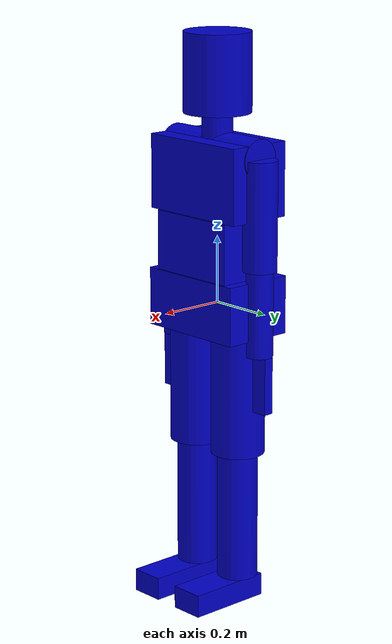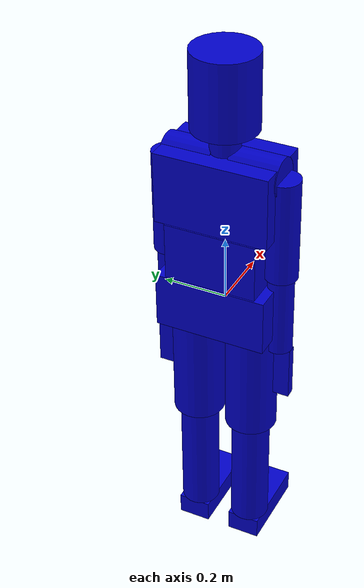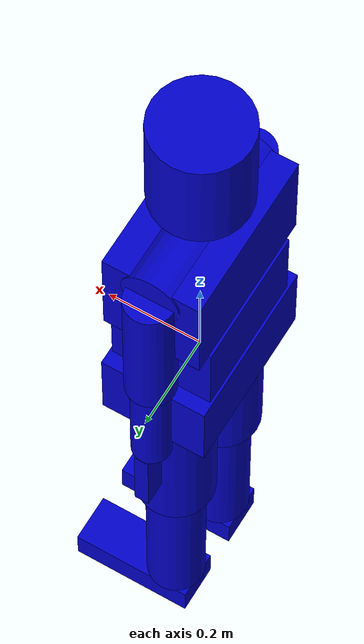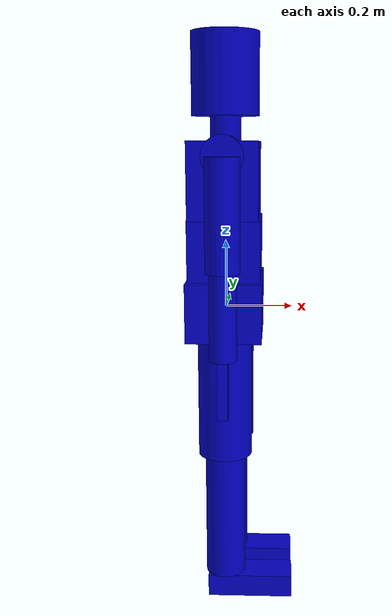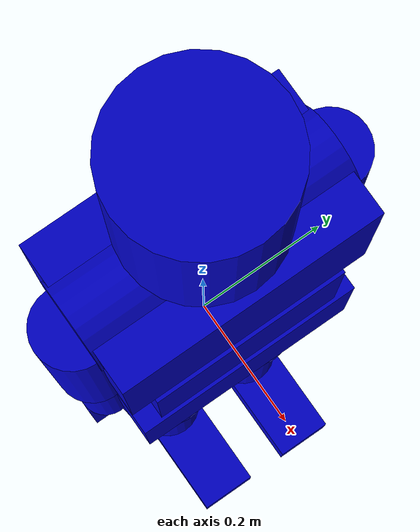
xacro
<?xml version="1.0"?>
  <robot  name="dhm" xmlns:xacro="http://www.ros.org/wiki/xacro">

	<!-- These values must be entered manually -->
	<!-- Average BMI = 22. If above, enter 1, else enter 0 -->
	<xacro:property name="bodyHeight" value="1.7" />
	<xacro:property name="bodyMass" value="65" />
	<xacro:property name="isBMIgreaterThanAverage" value="1"/>
	<!-- From now on, nothing should be changed in the file -->

	<xacro:property name="BMI" value="${bodyMass/(bodyHeight*bodyHeight)}" />
	<xacro:property name="PI" value="3.1415926535897931"/>

	<!-- Joint maximal velocity (guessed) -->
	<xacro:property name="maxVelJoint" value="1.0" />

	<!-- Scaling factor for joint maximal torque capacity (real capacity = factor * average human capacity)-->
	<xacro:property name="forceCapacity" value="1.0" />

	<!-- Joint dynamic properties -->
	<xacro:property name="jointDamping" value="0.01" />
	<xacro:property name="jointFriction" value="0.0" />

	<!-- Define length of body segments from total body bodyHeight -->
	<xacro:property name="ankleHeight" value="${bodyHeight*0.04}" />
	<xacro:property name="kneeHeight" value="${bodyHeight*0.27}" />
	<xacro:property name="hipHeight" value="${bodyHeight*0.53}" />
	<xacro:property name="shoulderHeight" value="${bodyHeight*0.82}" />
	<xacro:property name="hipWidth" value="${bodyHeight*0.105}" />
	<xacro:property name="armSpan" value="${bodyHeight*1.09}" />
	<xacro:property name="handLength" value="${bodyHeight*0.1}" />
	<xacro:property name="footLength" value="${bodyHeight*0.152}" />

	<xacro:property name="S5_L5" value="${0.055*bodyHeight}" />
	<xacro:property name="L5_T12" value="${0.105*bodyHeight}" />
	<xacro:property name="T12_C7" value="${0.13*bodyHeight}" />
	<xacro:property name="CSJ_C7" value="${0.025*bodyHeight}" />
	<xacro:property name="T12_CSJ" value="${T12_C7 - CSJ_C7}" />
	<xacro:property name="C7_C1" value="${0.055*bodyHeight}" />
	<xacro:property name="C1_headtop" value="${0.125*bodyHeight}" />
	<xacro:property name="headbase_headtop" value="${1.1*C1_headtop}" />

	<xacro:property name="shoulder_elbow" value="${bodyHeight*0.19}" />
	<xacro:property name="elbow_wrist" value="${bodyHeight*0.15}" />
	<xacro:property name="spine_shoulder" value="${0.5*armSpan - shoulder_elbow - elbow_wrist - handLength}" />
	<xacro:property name="CSJ_spine" value="${0.15*spine_shoulder}" />
	<xacro:property name="CSJ_shoulder" value="${spine_shoulder-CSJ_spine}" />

	<xacro:property name="S5_hip_horizontal" value="${0.5*hipWidth}" />
	<xacro:property name="hip_knee" value="${hipHeight-kneeHeight}" />
	<xacro:property name="knee_ankle" value="${kneeHeight-ankleHeight}" />

	<!-- Define thickness of body segment from BMI -->
	<xacro:property name="slimBMI" value="17" />
	<xacro:property name="normBMI" value="22" />
	<xacro:property name="fatBMI" value="40" />
	<xacro:property name="slimAlpha" value="0.9" />
	<xacro:property name="normAlpha" value="1.0" />
	<xacro:property name="fatAlpha" value="1.3" />

	<xacro:if value="${isBMIgreaterThanAverage == 1}">
		<xacro:property name="alpha" value="${1 + (fatAlpha  - normAlpha) * (BMI - normBMI) / (fatBMI - normBMI)}" />-->
	</xacro:if>
	<xacro:if value="${isBMIgreaterThanAverage == 0}">
		<xacro:property name="alpha" value="${1 - (normAlpha - slimAlpha) * (normBMI - BMI) / (normBMI - slimBMI)}" />-->
	</xacro:if>

	<!-- Define body segments shapes -->
	<!-- For collision shapes, pelvis and lumbarspine width is scaled by a factor collision_width_factor to enable arms along body without collision issues with the torso -->
	<xacro:property name="collision_width_factor" value="0.75"/>

	<xacro:property name="hip_thickness" value="${alpha*0.08}" />

	<xacro:property name="pelvis_length" value="${S5_L5 + hip_thickness}" />
	<xacro:property name="pelvis_width" value="${hipWidth + 0.7*hip_thickness + alpha*0.11}" />
	<xacro:property name="pelvis_depth" value="${2*alpha*0.11}" />

	<xacro:property name="lumbarspine_length" value="${L5_T12}" />
	<xacro:property name="lumbarspine_width" value="${hipWidth+alpha*0.105}" />
	<xacro:property name="lumbarspine_depth" value="${2*alpha*0.105}" />

	<xacro:property name="thoracicspine_length" value="${T12_C7}" />
	<xacro:property name="thoracicspine_width" value="${2*0.7*spine_shoulder+alpha*0.10}" />
	<xacro:property name="thoracicspine_depth" value="${2*alpha*0.10}" />

	<xacro:property name="neck_length" value="${C7_C1}" />
	<xacro:property name="neck_radius" value="${alpha*0.045}" />

	<xacro:property name="head_length" value="${headbase_headtop}" />
	<xacro:property name="head_radius" value="${0.1}" />

	<xacro:property name="clavicular_length" value="${CSJ_shoulder}" />
	<xacro:property name="clavicular_radius" value="${alpha*0.06}" />

	<xacro:property name="arm_length" value="${shoulder_elbow}" />
	<xacro:property name="arm_radius" value="${alpha*0.05}" />

	<xacro:property name="forearm_length" value="${elbow_wrist}" />
	<xacro:property name="forearm_radius" value="${alpha*0.04}" />

	<xacro:property name="hand_length" value="${handLength}" />
	<xacro:property name="hand_width" value="${2*alpha*0.04}" />
	<xacro:property name="hand_depth" value="${2*alpha*0.015}" />

	<xacro:property name="thigh_length" value="${hip_knee}" />
	<xacro:property name="thigh_radius" value="${alpha*0.08}" />

	<xacro:property name="shank_length" value="${knee_ankle}" />
	<xacro:property name="shank_radius" value="${alpha*0.06}" />

	<xacro:property name="foot_length" value="${footLength}" />
	<xacro:property name="foot_width" value="${0.4*footLength}" />
	<xacro:property name="foot_depth" value="${ankleHeight}" />

	<!-- Define mass normalization value and segment masses -->

	<!-- Mass of virtual bodies must be taken into account to have the correct full mass -->
	<xacro:property name="nb_virtualBodies" value="25" />

	<xacro:property name="massNorm" value="${-0.0426 + 1.00096*bodyMass + 0.00058*bodyHeight*100 + nb_virtualBodies*virtual_mass}" />

	<xacro:property name="lowertorso_mass" value="${bodyMass * (-7.498 + 0.0976*bodyMass + 0.04896*bodyHeight*100) / massNorm}" />
	<xacro:property name="middletorso_mass" value="${bodyMass * (7.181 + 0.2234*bodyMass - 0.0663*bodyHeight*100) / massNorm}" />
	<xacro:property name="uppertorso_mass" value="${bodyMass * (8.2144 + 0.1862*bodyMass - 0.0584*bodyHeight*100) / massNorm}" />
	<xacro:property name="pelvis_mass" value="${lowertorso_mass}" />
	<xacro:property name="lumbarspine_mass" value="${middletorso_mass}" />
	<xacro:property name="thoracicspine_mass" value="${(1.0-0.1)*uppertorso_mass}" />
	<xacro:property name="neckandhead_mass" value="${bodyMass * (1.296 + 0.0171*bodyMass + 0.0143*bodyHeight*100) / massNorm}" />
	<xacro:property name="neck_mass" value="${0.1*neckandhead_mass}" />
	<xacro:property name="head_mass" value="${0.9*neckandhead_mass}" />
	<xacro:property name="clavicular_mass" value="${0.05*uppertorso_mass}" />
	<xacro:property name="arm_mass" value="${bodyMass * (0.25 + 0.03012*bodyMass - 0.0027*bodyHeight*100) / massNorm}" />
	<xacro:property name="forearm_mass" value="${bodyMass * (0.3185 + 0.01445*bodyMass - 0.00114*bodyHeight*100) / massNorm}" />
	<xacro:property name="hand_mass" value="${bodyMass * (-0.1165 + 0.0036*bodyMass + 0.00175*bodyHeight*100) / massNorm}" />
	<xacro:property name="thigh_mass" value="${bodyMass * (-2.649 + 0.1463*bodyMass + 0.0137*bodyHeight*100) / massNorm}" />
	<xacro:property name="shank_mass" value="${bodyMass * (-1.592 + 0.03616*bodyMass + 0.0121*bodyHeight*100) / massNorm}" />
	<xacro:property name="foot_mass" value="${bodyMass * (-0.829 + 0.0077*bodyMass + 0.0073*bodyHeight*100) / massNorm}" />

	<!-- Macro which computes a shape (box or cylinder) inertia -->
	<!-- The lengths Lx, Ly and Lz are in the segment inertial frame (and not in the segment base frame, i.e. joint frame) -->
	<!-- For teh cylinder, the cylinder axis is along Z -->
	<xacro:macro name="box_inertia" params="m Lx Ly Lz">
		<inertia ixx="${1/12 * m * (Ly*Ly + Lz*Lz)}" ixy="0" ixz="0" iyy="${1/12 * m * (Lx*Lx + Lz*Lz)}" iyz="0" izz="${1/12 * m * (Lx*Lx + Ly*Ly)}" />
	</xacro:macro>
	<xacro:macro name="cylinder_inertia" params="m L r">
		<inertia ixx="${1/12 * m * (3*r*r + L*L)}" ixy="0" ixz="0" iyy="${1/12 * m * (3*r*r + L*L)}" iyz="0" izz="${1/2 * m * r*r}" />
	</xacro:macro>
	<xacro:macro name="sphere_inertia" params="m r">
		<inertia ixx="${2/5 * m * r*r}" ixy="0" ixz="0" iyy="${2/5 * m * r*r}" iyz="0" izz="${2/5 * m * r*r}" />
	</xacro:macro>

	<xacro:property name="virtual_mass" value="0.1" />
	<xacro:property name="virtual_radius" value="0.03" />
	<xacro:macro name="virtual_body" params="name">
		<link name="${name}">
			<inertial>
				<mass value="${virtual_mass}" />
				<origin xyz="0 0 0" rpy="0 0 0" />
				<xacro:sphere_inertia m="${virtual_mass}" r="${virtual_radius}"/>
			</inertial>
		</link>
	</xacro:macro>

	<!-- Materials -->
	<material name="blue">
		<color rgba="0 0 0.8 1"/>
	</material>

	<!-- Define bodies -->
	<xacro:virtual_body name="root" />

	<link name="pelvis">
		<visual>
			<geometry>
				<box size="${pelvis_depth} ${pelvis_length} ${pelvis_width}"/>
			</geometry>
			<origin rpy="0 0 0" xyz="0 ${pelvis_length/2-hip_thickness} 0"/>
			<material name="blue" />
		</visual>
		<collision>
			<geometry>
				<box size="${pelvis_depth} ${pelvis_length} ${collision_width_factor*pelvis_width}"/>
			</geometry>
			<origin rpy="0 0 0" xyz="0 ${pelvis_length/2-hip_thickness} 0"/>
		</collision>
		<inertial>
			<mass value="${pelvis_mass}" />
			<origin rpy="0 0 0" xyz="0 ${pelvis_length/2-hip_thickness} 0"/>
			<xacro:box_inertia m="${pelvis_mass}" Lx="${pelvis_depth}" Ly="${pelvis_length}" Lz="${pelvis_width}"/>
		</inertial>
	</link>

	<xacro:virtual_body name="body_L5_1" />
	<xacro:virtual_body name="body_L5_2" />

	<link name="lumbar_spine">
		<visual>
			<geometry>
				<box size="${lumbarspine_depth}  ${lumbarspine_length} ${lumbarspine_width}"/>
			</geometry>
 			<origin rpy="0 0 0" xyz="0 ${lumbarspine_length/2} 0"/>
			<material name="blue" />
		</visual>
		<collision>
			<geometry>
				<box size="${lumbarspine_depth}  ${lumbarspine_length} ${collision_width_factor*lumbarspine_width}"/>
			</geometry>
			<origin rpy="0 0 0" xyz="0 ${lumbarspine_length/2} 0"/>
		</collision>
		<inertial>
			<mass value="${lumbarspine_mass}" />
			<origin rpy="0 0 0" xyz="0 ${lumbarspine_length/2} 0"/>
			<xacro:box_inertia m="${lumbarspine_mass}" Lx="${lumbarspine_depth}" Ly="${lumbarspine_length}" Lz="${lumbarspine_width}"/>
		</inertial>
	</link>

	<xacro:virtual_body name="body_T12_1" />
	<xacro:virtual_body name="body_T12_2" />

	<link name="thoracic_spine">
		<visual>
			<geometry>
				<box size="${thoracicspine_depth} ${thoracicspine_length} ${thoracicspine_width}"/>
			</geometry>
			<origin rpy="0 0 0" xyz="0 ${thoracicspine_length/2} 0"/>
			<material name="blue" />
		</visual>
		<collision>
			<geometry>
				<box size="${thoracicspine_depth} ${thoracicspine_length} ${thoracicspine_width}"/>
			</geometry>
			<origin rpy="0 0 0" xyz="0 ${thoracicspine_length/2} 0"/>
		</collision>
		<inertial>
			<mass value="${thoracicspine_mass}" />
			<origin rpy="0 0 0" xyz="0 ${thoracicspine_length/2} 0"/>
			<xacro:box_inertia m="${thoracicspine_mass}" Lx="${thoracicspine_depth}" Ly="${thoracicspine_length}" Lz="${thoracicspine_width}"/>
		</inertial>
	</link>

	<xacro:virtual_body name="body_C7_1" />
	<xacro:virtual_body name="body_C7_2" />

	<link name="neck">
		<visual>
			<geometry>
				<cylinder length="${neck_length}" radius="${neck_radius}" />
			</geometry>
			<origin rpy="${-PI/2} 0 0" xyz="0 ${neck_length/2} 0"/>
			<material name="blue" />
		</visual>
		<collision>
			<geometry>
				<cylinder length="${neck_length}" radius="${neck_radius}" />
			</geometry>
			<origin rpy="${-PI/2} 0 0" xyz="0 ${neck_length/2} 0"/>
		</collision>
		<inertial>
			<mass value="${neck_mass}" />
			<origin rpy="${-PI/2} 0 0" xyz="0 ${neck_length/2} 0"/>
			<xacro:cylinder_inertia m="${neck_mass}" L="${neck_length}" r="${neck_radius}" />
		</inertial>
	</link>

	<xacro:virtual_body name="body_C1" />

	<link name="head">
		<visual>
			<geometry>
				<cylinder length="${head_length}" radius="${head_radius}"/>
			</geometry>
			<origin rpy="${-PI/2} 0 0" xyz="0 ${C1_headtop - headbase_headtop/2} 0"/>
			<material name="blue" />
		</visual>
		<collision>
			<geometry>
				<cylinder length="${head_length}" radius="${head_radius}"/>
			</geometry>
			<origin rpy="${-PI/2} 0 0" xyz="0 ${C1_headtop - headbase_headtop/2} 0"/>
		</collision>
		<inertial>
			<mass value="${head_mass}" />
			<origin rpy="${-PI/2} 0 0" xyz="0 ${C1_headtop - headbase_headtop/2} 0"/>
			<xacro:cylinder_inertia m="${head_mass}" L="${head_length}" r="${head_radius}" />
		</inertial>
	</link>

	<xacro:virtual_body name="body_CSJ_right_clavicular" />

	<link name="right_clavicular">
		<visual>
			<geometry>
				<cylinder length="${clavicular_length}" radius="${clavicular_radius}"/>
			</geometry>
			<origin  rpy="0 0 0" xyz="0 0 ${clavicular_length/2}"/>
			<material name="blue" />
		</visual>
		<inertial>
			<mass value="${clavicular_mass}" />
			<origin  rpy="0 0 0" xyz="0 0 ${clavicular_length/2}"/>
			<xacro:cylinder_inertia m="${clavicular_mass}" L="${clavicular_length}" r="${clavicular_radius}" />
		</inertial>
	</link>

	<xacro:virtual_body name="body_right_shoulder_1" />
	<xacro:virtual_body name="body_right_shoulder_2" />

	<link name="right_arm">
		<visual>
			<geometry>
				<cylinder length="${arm_length}" radius="${arm_radius}"/>
			</geometry>
			<origin rpy="${PI/2} 0 0" xyz="0 ${-arm_length/2} 0"/>
			<material name="blue" />
		</visual>
		<collision>
			<geometry>
				<cylinder length="${arm_length}" radius="${arm_radius}"/>
			</geometry>
			<origin rpy="${PI/2} 0 0" xyz="0 ${-arm_length/2} 0"/>
		</collision>
		<inertial>
			<mass value="${arm_mass}" />
			<origin rpy="${PI/2} 0 0" xyz="0 ${-arm_length/2} 0"/>
			<xacro:cylinder_inertia m="${arm_mass}" L="${arm_length}" r="${arm_radius}" />
		</inertial>
	</link>

	<xacro:virtual_body name="body_right_elbow" />

	<link name="right_forearm">
		<visual>
			<geometry>
				<cylinder length="${forearm_length}" radius="${forearm_radius}"/>
			</geometry>
			<origin rpy="${PI/2} 0 0" xyz="0 ${-forearm_length/2} 0"/>
			<material name="blue" />
		</visual>
		<collision>
			<geometry>
				<cylinder length="${forearm_length}" radius="${forearm_radius}"/>
			</geometry>
			<origin rpy="${PI/2} 0 0" xyz="0 ${-forearm_length/2} 0"/>
		</collision>
		<inertial>
			<mass value="${forearm_mass}" />
			<origin rpy="${PI/2} 0 0" xyz="0 ${-forearm_length/2} 0"/>
			<xacro:cylinder_inertia m="${forearm_mass}" L="${forearm_length}" r="${forearm_radius}" />
		</inertial>
	</link>

	<xacro:virtual_body name="body_right_wrist" />

	<link name="right_hand">
		<visual>
			<geometry>
				<box size="${hand_depth} ${hand_length} ${hand_width}"/>
			</geometry>
			<origin rpy="0 0 0" xyz="0 ${-hand_length/2} 0"/>
			<material name="blue" />
		</visual>
		<collision>
			<geometry>
				<box size="${hand_depth} ${hand_length} ${hand_width}"/>
			</geometry>
			<origin rpy="0 0 0" xyz="0 ${-hand_length/2} 0"/>
		</collision>
		<inertial>
			<mass value="${hand_mass}" />
			<origin rpy="0 0 0" xyz="0 ${-hand_length/2} 0" />
			<xacro:box_inertia m="${hand_mass}" Lx="${hand_depth}" Ly="${hand_length}" Lz="${hand_width}"/>
		</inertial>
	</link>

	<xacro:virtual_body name="body_CSJ_left_clavicular" />

	<link name="left_clavicular">
		<visual>
			<geometry>
				<cylinder length="${clavicular_length}" radius="${clavicular_radius}"/>
			</geometry>
			<origin  rpy="0 0 0" xyz="0 0 ${-clavicular_length/2}"/>
			<material name="blue" />
		</visual>
		<inertial>

			<mass value="${clavicular_mass}" />
			<origin  rpy="0 0 0" xyz="0 0 ${-clavicular_length/2}"/>
			<xacro:cylinder_inertia m="${clavicular_mass}" L="${clavicular_length}" r="${clavicular_radius}" />
		</inertial>
	</link>

	<xacro:virtual_body name="body_left_shoulder_1" />
	<xacro:virtual_body name="body_left_shoulder_2" />

	<link name="left_arm">
		<visual>
			<geometry>
				<cylinder length="${arm_length}" radius="${arm_radius}"/>
			</geometry>
			<origin rpy="${PI/2} 0 0" xyz="0 ${-arm_length/2} 0"/>
			<material name="blue" />
		</visual>
		<collision>
			<geometry>
				<cylinder length="${arm_length}" radius="${arm_radius}"/>
			</geometry>
			<origin rpy="${PI/2} 0 0" xyz="0 ${-arm_length/2} 0"/>
		</collision>
		<inertial>
			<mass value="${arm_mass}" />
			<origin rpy="${PI/2} 0 0" xyz="0 ${-arm_length/2} 0"/>>
			<xacro:cylinder_inertia m="${arm_mass}" L="${arm_length}" r="${arm_radius}" />
		</inertial>
	</link>

	<xacro:virtual_body name="body_left_elbow" />

	<link name="left_forearm">
		<visual>
			<geometry>
				<cylinder length="${forearm_length}" radius="${forearm_radius}"/>
			</geometry>
			<origin rpy="${PI/2} 0 0" xyz="0 ${-forearm_length/2} 0"/>
			<material name="blue" />
		</visual>
		<collision>
			<geometry>
				<cylinder length="${forearm_length}" radius="${forearm_radius}"/>
			</geometry>
			<origin rpy="${PI/2} 0 0" xyz="0 ${-forearm_length/2} 0"/>
		</collision>
		<inertial>
			<mass value="${forearm_mass}" />
			<origin rpy="${PI/2} 0 0" xyz="0 ${-forearm_length/2} 0"/>
			<xacro:cylinder_inertia m="${forearm_mass}" L="${forearm_length}" r="${forearm_radius}" />
		</inertial>
	</link>

	<xacro:virtual_body name="body_left_wrist" />

	<link name="left_hand">
		<visual>
			<geometry>
				<box size="${hand_depth} ${hand_length} ${hand_width}"/>
			</geometry>
			<origin rpy="0 0 0" xyz="0 ${-hand_length/2} 0"/>
			<material name="blue" />
		</visual>
		<collision>
			<geometry>
				<box size="${hand_depth} ${hand_length} ${hand_width}"/>
			</geometry>
			<origin rpy="0 0 0" xyz="0 ${-hand_length/2} 0"/>
		</collision>
		<inertial>
			<mass value="${hand_mass}" />
			<origin rpy="0 0 0" xyz="0 ${-hand_length/2} 0" />
			<xacro:box_inertia m="${hand_mass}" Lx="${hand_depth}" Ly="${hand_length}" Lz="${hand_width}"/>
		</inertial>
	</link>

	<xacro:virtual_body name="body_right_hip_1" />
	<xacro:virtual_body name="body_right_hip_2" />

	<link name="right_thigh">
		<visual>
			<geometry>
				<cylinder length="${thigh_length}" radius="${thigh_radius}"/>
			</geometry>
			<origin rpy="${PI/2} 0 0" xyz="0 ${-thigh_length/2} 0"/>
			<material name="blue" />
		</visual>
		<collision>
			<geometry>
				<cylinder length="${thigh_length}" radius="${thigh_radius}"/>
			</geometry>
			<origin rpy="${PI/2} 0 0" xyz="0 ${-thigh_length/2} 0"/>
		</collision>
		<inertial>
			<mass value="${thigh_mass}" />
			<origin rpy="${PI/2} 0 0" xyz="0 ${-thigh_length/2} 0"/>
			<xacro:cylinder_inertia m="${thigh_mass}" L="${thigh_length}" r="${thigh_radius}" />
		</inertial>
	</link>

	<xacro:virtual_body name="body_right_knee" />

	<link name="right_shank">
		<visual>
			<geometry>
				<cylinder length="${shank_length}" radius="${shank_radius}"/>
			</geometry>
			<origin rpy="${PI/2} 0 0" xyz="0 ${-shank_length/2} 0"/>
			<material name="blue" />
		</visual>
		<collision>
			<geometry>
				<cylinder length="${shank_length}" radius="${shank_radius}"/>
			</geometry>
			<origin rpy="${PI/2} 0 0" xyz="0 ${-shank_length/2} 0"/>
		</collision>
		<inertial>
			<mass value="${shank_mass}" />
			<origin rpy="${PI/2} 0 0" xyz="0 ${-shank_length/2} 0"/>
			<xacro:cylinder_inertia m="${shank_mass}" L="${shank_length}" r="${shank_radius}" />
		</inertial>
	</link>

	<xacro:virtual_body name="body_right_ankle" />

	<link name="right_foot">
		<visual>
			<geometry>
				<box size="${foot_length} ${foot_depth} ${foot_width}" />
			</geometry>
			<origin rpy="0 0 0" xyz="${foot_length/2-0.2*foot_length} ${-foot_depth/2} 0"/>
			<material name="blue" />
		</visual>
		<collision>
			<geometry>
				<box size="${foot_length} ${foot_depth} ${foot_width}" />
			</geometry>
			<origin rpy="0 0 0" xyz="${foot_length/2-0.2*foot_length} ${-foot_depth/2} 0"/>
		</collision>
		<inertial>
			<mass value="${foot_mass}" />
			<origin rpy="0 0 0" xyz="${foot_length/2-0.2*foot_length} ${-foot_depth/2} 0"/>
			<xacro:box_inertia m="${foot_mass}" Lx="${foot_length}" Ly="${foot_depth}" Lz="${foot_width}"/>
		</inertial>
	</link>

	<xacro:virtual_body name="body_left_hip_1" />
	<xacro:virtual_body name="body_left_hip_2" />

	<link name="left_thigh">
		<visual>
			<geometry>
				<cylinder length="${thigh_length}" radius="${thigh_radius}" />
			</geometry>
			<origin rpy="${PI/2} 0 0" xyz="0 ${-thigh_length/2} 0"/>
			<material name="blue" />
		</visual>
		<collision>
			<geometry>
				<cylinder length="${thigh_length}" radius="${thigh_radius}" />
			</geometry>
			<origin rpy="${PI/2} 0 0" xyz="0 ${-thigh_length/2} 0"/>
		</collision>
		<inertial>
			<mass value="${thigh_mass}" />
			<origin rpy="${PI/2} 0 0" xyz="0 ${-thigh_length/2} 0"/>
			<xacro:cylinder_inertia m="${thigh_mass}" L="${thigh_length}" r="${thigh_radius}" />
		</inertial>
	</link>

	<xacro:virtual_body name="body_left_knee" />

	<link name="left_shank">
		<visual>
			<geometry>
				<cylinder length="${shank_length}" radius="${shank_radius}" />
			</geometry>
			<origin rpy="${PI/2} 0 0" xyz="0 ${-shank_length/2} 0"/>
			<material name="blue" />
		</visual>
		<collision>
			<geometry>
				<cylinder length="${-shank_length}" radius="${shank_radius}" />
			</geometry>
			<origin rpy="${PI/2} 0 0" xyz="0 ${-shank_length/2} 0"/>
		</collision>
		<inertial>
			<mass value="${shank_mass}" />
			<origin rpy="${PI/2} 0 0" xyz="0 ${-shank_length/2} 0"/>
			<xacro:cylinder_inertia m="${shank_mass}" L="${shank_length}" r="${shank_radius}" />
		</inertial>
	</link>

	<xacro:virtual_body name="body_left_ankle" />

	<link name="left_foot">
		<visual>
			<geometry>
				<box size="${foot_length} ${foot_depth} ${foot_width}" />
			</geometry>
			<origin rpy="0 0 0" xyz="${foot_length/2-0.2*foot_length} ${-foot_depth/2} 0"/>
			<material name="blue" />
		</visual>
		<collision>
			<geometry>
				<box size="${foot_length} ${foot_depth} ${foot_width}" />
			</geometry>
			<origin rpy="0 0 0" xyz="${foot_length/2-0.2*foot_length} ${-foot_depth/2} 0"/>
		</collision>
		<inertial>
			<mass value="${foot_mass}" />
			<origin rpy="0 0 0" xyz="${foot_length/2-0.2*foot_length} ${-foot_depth/2} 0"/>
			<xacro:box_inertia m="${foot_mass}" Lx="${foot_length}" Ly="${foot_depth}" Lz="${foot_width}"/>
		</inertial>
	</link>

	<!-- Define joints -->
	<!-- Joint for correct pelvis orientation -->
	<joint name="root_ISB_orientation" type="fixed">
		<parent link="root" />
		<child link="pelvis" />
		<origin rpy="${PI/2} 0 0" xyz="0 0 0" />
	</joint>

	<!-- Back joints -->
	<joint name="lumbarspine_Y" type="revolute">
		<parent link="pelvis"/>
		<child link="body_L5_1"/>
		<axis xyz="0 1 0"/>
		<origin xyz="0 ${S5_L5} 0"/>
		<limit effort="${65*forceCapacity}" lower="${-20*PI/180}" upper="${20*PI/180}" velocity="${maxVelJoint}"/>
		<dynamics damping="${jointDamping}" friction="${jointFriction}"/>
	</joint>

	<joint name="lumbarspine_Z" type="revolute">
		<parent link="body_L5_1"/>
		<child link="body_L5_2"/>
		<axis xyz="0 0 1"/>
		<origin xyz="0 0 0"/>
		<limit effort="${228*forceCapacity}" lower="${-25*PI/180}" upper="${10*PI/180}" velocity="${maxVelJoint}"/>
		<dynamics damping="${jointDamping}" friction="${jointFriction}"/>
	</joint>

	<joint name="lumbarspine_X" type="revolute">
		<parent link="body_L5_2"/>
		<child link="lumbar_spine"/>
		<axis xyz="1 0 0"/>
		<origin xyz="0 0 0"/>
		<limit effort="${155*forceCapacity}" lower="${-15*PI/180}" upper="${15*PI/180}" velocity="${maxVelJoint}"/>
		<dynamics damping="${jointDamping}" friction="${jointFriction}"/>
	</joint>

	<joint name="thoracicspine_Y" type="revolute">
		<parent link="lumbar_spine"/>
		<child link="body_T12_1"/>
		<axis xyz="0 1 0"/>
		<origin xyz="0 ${L5_T12} 0"/>
		<limit effort="${65*forceCapacity}" lower="${-15*PI/180}" upper="${15*PI/180}" velocity="${maxVelJoint}"/>
		<dynamics damping="${jointDamping}" friction="${jointFriction}"/>
	</joint>

	<joint name="thoracicspine_Z" type="revolute">
		<parent link="body_T12_1"/>
		<child link="body_T12_2"/>
		<axis xyz="0 0 1"/>
		<origin xyz="0 0 0"/>
		<limit effort="${228*forceCapacity}" lower="${-25*PI/180}" upper="${10*PI/180}" velocity="${maxVelJoint}"/>
		<dynamics damping="${jointDamping}" friction="${jointFriction}"/>
	</joint>

	<joint name="thoracicspine_X" type="revolute">
		<parent link="body_T12_2"/>
		<child link="thoracic_spine"/>
		<axis xyz="1 0 0"/>
		<origin xyz="0 0 0"/>
		<limit effort="${155*forceCapacity}" lower="${-15*PI/180}" upper="${15*PI/180}" velocity="${maxVelJoint}"/>
		<dynamics damping="${jointDamping}" friction="${jointFriction}"/>
	</joint>

	<joint name="neck_Y" type="revolute">
		<parent link="thoracic_spine"/>
		<child link="body_C7_1"/>
		<axis xyz="0 1 0"/>
		<origin xyz="0 ${T12_C7} 0"/>
		<limit effort="50" lower="${-85*PI/180}" upper="${85*PI/180}" velocity="${maxVelJoint}"/>
		<dynamics damping="${jointDamping}" friction="${jointFriction}"/>
	</joint>

	<joint name="neck_Z" type="revolute">
		<parent link="body_C7_1"/>
		<child link="body_C7_2"/>
		<axis xyz="0 0 1"/>
		<origin xyz="0 0 0"/>
		<limit effort="50" lower="${-45*PI/180}" upper="${25*PI/180}" velocity="${maxVelJoint}"/>
		<dynamics damping="${jointDamping}" friction="${jointFriction}"/>
	</joint>

	<joint name="neck_X" type="revolute">
		<parent link="body_C7_2"/>
		<child link="neck"/>
		<axis xyz="1 0 0"/>
		<origin xyz="0 0 0"/>
		<limit effort="50" lower="${-25*PI/180}" upper="${25*PI/180}" velocity="${maxVelJoint}"/>
		<dynamics damping="${jointDamping}" friction="${jointFriction}"/>
	</joint>

	<joint name="head_Z" type="revolute">
		<parent link="neck"/>
		<child link="body_C1"/>
		<axis xyz="0 0 1"/>
		<origin xyz="0 ${C7_C1} 0"/>
		<limit effort="20" lower="${-40*PI/180}" upper="${25*PI/180}" velocity="${maxVelJoint}"/>
		<dynamics damping="${jointDamping}" friction="${jointFriction}"/>
	</joint>

	<joint name="head_X" type="revolute">
		<parent link="body_C1"/>
		<child link="head"/>
		<axis xyz="1 0 0"/>
		<origin xyz="0 0 0"/>
		<limit effort="20" lower="${-25*PI/180}" upper="${25*PI/180}" velocity="${maxVelJoint}"/>
		<dynamics damping="${jointDamping}" friction="${jointFriction}"/>
	</joint>

	<!-- Right arm joints -->
	<joint name="right_clavicular_X" type="revolute">
		<parent link="thoracic_spine"/>
		<child link="body_CSJ_right_clavicular"/>
		<axis xyz="1 0 0"/>
		<origin xyz="0 ${T12_CSJ} ${CSJ_spine}"/>
		<limit effort="${105*forceCapacity}" lower="${-40*PI/180}" upper="${10*PI/180}" velocity="${maxVelJoint}"/>
		<dynamics damping="${jointDamping}" friction="${jointFriction}"/>
	</joint>

	<joint name="right_clavicular_Y" type="revolute">
		<parent link="body_CSJ_right_clavicular"/>
		<child link="right_clavicular"/>
		<axis xyz="0 1 0"/>
		<origin xyz="0 0 0"/>
		<limit effort="${107*forceCapacity}" lower="${-15*PI/180}" upper="${20*PI/180}" velocity="${maxVelJoint}"/>
		<dynamics damping="${jointDamping}" friction="${jointFriction}"/>
	</joint>

	<joint name="right_shoulder_Y" type="revolute">
		<parent link="right_clavicular"/>
		<child link="body_right_shoulder_1"/>
		<axis xyz="0 1 0"/>
		<origin xyz="0 0 ${CSJ_shoulder}"/>
		<limit effort="${51*forceCapacity}" lower="${-34*PI/180}" upper="${97*PI/180}" velocity="${maxVelJoint}"/>
		<dynamics damping="${jointDamping}" friction="${jointFriction}"/>
	</joint>

	<joint name="right_shoulder_Z" type="revolute">
		<parent link="body_right_shoulder_1"/>
		<child link="body_right_shoulder_2"/>
		<axis xyz="0 0 1"/>
		<origin xyz="0 0 0"/>
		<limit effort="${90*forceCapacity}" lower="${-61*PI/180}" upper="${188*PI/180}" velocity="${maxVelJoint}"/>
		<dynamics damping="${jointDamping}" friction="${jointFriction}"/>
	</joint>

	<joint name="right_shoulder_X" type="revolute">
		<parent link="body_right_shoulder_2"/>
		<child link="right_arm"/>
		<axis xyz="1 0 0"/>
		<origin xyz="0 0 0"/>
		<limit effort="${69*forceCapacity}" lower="${-134*PI/180}" upper="${48*PI/180}" velocity="${maxVelJoint}"/>
		<dynamics damping="${jointDamping}" friction="${jointFriction}"/>
	</joint>

	<joint name="right_elbow_Z" type="revolute">
		<parent link="right_arm"/>
		<child link="body_right_elbow"/>
		<axis xyz="0 0 1"/>
		<origin xyz="0 ${-shoulder_elbow} 0"/>
		<limit effort="${75*forceCapacity}" lower="${-5*PI/180}" upper="${142*PI/180}" velocity="${maxVelJoint}"/>
		<dynamics damping="${jointDamping}" friction="${jointFriction}"/>
	</joint>

	<joint name="right_elbow_Y" type="revolute">
		<parent link="body_right_elbow"/>
		<child link="right_forearm"/>
		<axis xyz="0 1 0"/>
		<origin xyz="0 0 0"/>
		<limit effort="${13*forceCapacity}" lower="${-23*PI/180}" upper="${167*PI/180}" velocity="${maxVelJoint}"/>
		<dynamics damping="${jointDamping}" friction="${jointFriction}"/>
	</joint>

	<joint name="right_wrist_Z" type="revolute">
		<parent link="right_forearm"/>
		<child link="body_right_wrist"/>
		<axis xyz="0 0 1"/>
		<origin xyz="0 ${-elbow_wrist} 0"/>
		<limit effort="${10*forceCapacity}" lower="${-99*PI/180}" upper="${90*PI/180}" velocity="${maxVelJoint}"/>
		<dynamics damping="${jointDamping}" friction="${jointFriction}"/>
	</joint>

	<joint name="right_wrist_X" type="revolute">
		<parent link="body_right_wrist"/>
		<child link="right_hand"/>
		<axis xyz="1 0 0"/>
		<origin xyz="0 0 0"/>
		<limit effort="${11*forceCapacity}" lower="${-47*PI/180}" upper="${27*PI/180}" velocity="${maxVelJoint}"/>
		<dynamics damping="${jointDamping}" friction="${jointFriction}"/>
	</joint>

	<!-- Left arm joints -->
	<joint name="left_clavicular_X" type="revolute">
		<parent link="thoracic_spine"/>
		<child link="body_CSJ_left_clavicular"/>
		<axis xyz="1 0 0"/>
		<origin xyz="0 ${T12_CSJ} ${-CSJ_spine}"/>
		<limit effort="${105*forceCapacity}" lower="${-10*PI/180}" upper="${40*PI/180}" velocity="${maxVelJoint}"/>
		<dynamics damping="${jointDamping}" friction="${jointFriction}"/>
	</joint>

	<joint name="left_clavicular_Y" type="revolute">
		<parent link="body_CSJ_left_clavicular"/>
		<child link="left_clavicular"/>
		<axis xyz="0 1 0"/>
		<origin xyz="0 0 0"/>
		<limit effort="${107*forceCapacity}" lower="${-20*PI/180}" upper="${15*PI/180}" velocity="${maxVelJoint}"/>
		<dynamics damping="${jointDamping}" friction="${jointFriction}"/>
	</joint>

	<joint name="left_shoulder_Y" type="revolute">
		<parent link="left_clavicular"/>
		<child link="body_left_shoulder_1"/>
		<axis xyz="0 1 0"/>
		<origin xyz="0 0 ${-CSJ_shoulder}"/>
		<limit effort="${51*forceCapacity}" lower="${-97*PI/180}" upper="${34*PI/180}" velocity="${maxVelJoint}"/>
		<dynamics damping="${jointDamping}" friction="${jointFriction}"/>
	</joint>

	<joint name="left_shoulder_Z" type="revolute">
		<parent link="body_left_shoulder_1"/>
		<child link="body_left_shoulder_2"/>
		<axis xyz="0 0 1"/>
		<origin xyz="0 0 0"/>
		<limit effort="${90*forceCapacity}" lower="${-61*PI/180}" upper="${188*PI/180}" velocity="${maxVelJoint}"/>
		<dynamics damping="${jointDamping}" friction="${jointFriction}"/>
	</joint>

	<joint name="left_shoulder_X" type="revolute">
		<parent link="body_left_shoulder_2"/>
		<child link="left_arm"/>
		<axis xyz="1 0 0"/>
		<origin xyz="0 0 0"/>
		<limit effort="${69*forceCapacity}" lower="${-48*PI/180}" upper="${134*PI/180}" velocity="${maxVelJoint}"/>
		<dynamics damping="${jointDamping}" friction="${jointFriction}"/>
	</joint>

	<joint name="left_elbow_Z" type="revolute">
		<parent link="left_arm"/>
		<child link="body_left_elbow"/>
		<axis xyz="0 0 1"/>
		<origin xyz="0 ${-shoulder_elbow} 0"/>
		<limit effort="${75*forceCapacity}" lower="${-5*PI/180}" upper="${142*PI/180}" velocity="${maxVelJoint}"/>
		<dynamics damping="${jointDamping}" friction="${jointFriction}"/>
	</joint>

	<joint name="left_elbow_Y" type="revolute">
		<parent link="body_left_elbow"/>
		<child link="left_forearm"/>
		<axis xyz="0 1 0"/>
		<origin xyz="0 0 0"/>
		<limit effort="${13*forceCapacity}" lower="${-167*PI/180}" upper="${23*PI/180}" velocity="${maxVelJoint}"/>
		<dynamics damping="${jointDamping}" friction="${jointFriction}"/>
	</joint>

	<joint name="left_wrist_Z" type="revolute">
		<parent link="left_forearm"/>
		<child link="body_left_wrist"/>
		<axis xyz="0 0 1"/>
		<origin xyz="0 ${-elbow_wrist} 0"/>
		<limit effort="${10*forceCapacity}" lower="${-90*PI/180}" upper="${99*PI/180}" velocity="${maxVelJoint}"/>
		<dynamics damping="${jointDamping}" friction="${jointFriction}"/>
	</joint>

	<joint name="left_wrist_X" type="revolute">
		<parent link="body_left_wrist"/>
		<child link="left_hand"/>
		<axis xyz="1 0 0"/>
		<origin xyz="0 0 0"/>
		<limit effort="${11*forceCapacity}" lower="${-27*PI/180}" upper="${47*PI/180}" velocity="${maxVelJoint}"/>
		<dynamics damping="${jointDamping}" friction="${jointFriction}"/>
	</joint>

	<!-- Right leg joints -->
	<joint name="right_hip_Y" type="revolute">
		<parent link="pelvis"/>
		<child link="body_right_hip_1"/>
		<axis xyz="0 1 0"/>
		<origin xyz="0 0 ${S5_hip_horizontal}"/>
		<limit effort="${67*forceCapacity}" lower="${-34*PI/180}" upper="${39*PI/180}" velocity="${maxVelJoint}"/>
		<dynamics damping="${jointDamping}" friction="${jointFriction}"/>
	</joint>

	<joint name="right_hip_Z" type="revolute">
		<parent link="body_right_hip_1"/>
		<child link="body_right_hip_2"/>
		<axis xyz="0 0 1"/>
		<origin xyz="0 0 0"/>
		<limit effort="${186*forceCapacity}" lower="${-15*PI/180}" upper="${113*PI/180}" velocity="${maxVelJoint}"/>
		<dynamics damping="${jointDamping}" friction="${jointFriction}"/>
	</joint>

	<joint name="right_hip_X" type="revolute">
		<parent link="body_right_hip_2"/>
		<child link="right_thigh"/>
		<axis xyz="1 0 0"/>
		<origin xyz="0 0 0"/>
		<limit effort="${108*forceCapacity}" lower="${-53*PI/180}" upper="${31*PI/180}" velocity="${maxVelJoint}"/>
		<dynamics damping="${jointDamping}" friction="${jointFriction}"/>
	</joint>

	<joint name="right_knee_Y" type="revolute">
		<parent link="right_thigh"/>
		<child link="body_right_knee"/>
		<axis xyz="0 1 0"/>
		<origin xyz="0 ${-hip_knee} 0"/>
		<limit effort="${22*forceCapacity}" lower="${-43*PI/180}" upper="${35*PI/180}" velocity="${maxVelJoint}"/>
		<dynamics damping="${jointDamping}" friction="${jointFriction}"/>
	</joint>

	<joint name="right_knee_Z" type="revolute">
		<parent link="body_right_knee"/>
		<child link="right_shank"/>
		<axis xyz="0 0 1"/>
		<origin xyz="0 0 0"/>
		<limit effort="${164*forceCapacity}" lower="${-140*PI/180}" upper="${5*PI/180}" velocity="${maxVelJoint}"/>
		<dynamics damping="${jointDamping}" friction="${jointFriction}"/>
	</joint>

	<joint name="right_ankle_Z" type="revolute">
		<parent link="right_shank"/>
		<child link="body_right_ankle"/>
		<axis xyz="0 0 1"/>
		<origin xyz="0 ${-knee_ankle} 0"/>
		<limit effort="${123*forceCapacity}" lower="${-38*PI/180}" upper="${35*PI/180}" velocity="${maxVelJoint}"/>
		<dynamics damping="${jointDamping}" friction="${jointFriction}"/>
	</joint>

	<joint name="right_ankle_X" type="revolute">
		<parent link="body_right_ankle"/>
		<child link="right_foot"/>
		<axis xyz="1 0 0"/>
		<origin xyz="0 0 0"/>
		<limit effort="${29*forceCapacity}" lower="${-24*PI/180}" upper="${23*PI/180}" velocity="${maxVelJoint}"/>
		<dynamics damping="${jointDamping}" friction="${jointFriction}"/>
	</joint>

	<!-- Left leg joints -->
	<joint name="left_hip_Y" type="revolute">
		<parent link="pelvis"/>
		<child link="body_left_hip_1"/>
		<axis xyz="0 1 0"/>
		<origin xyz="0 0 ${-S5_hip_horizontal}"/>
		<limit effort="${67*forceCapacity}" lower="${-39*PI/180}" upper="${34*PI/180}" velocity="${maxVelJoint}"/>
		<dynamics damping="${jointDamping}" friction="${jointFriction}"/>
	</joint>

	<joint name="left_hip_Z" type="revolute">
		<parent link="body_left_hip_1"/>
		<child link="body_left_hip_2"/>
		<axis xyz="0 0 1"/>
		<origin xyz="0 0 0"/>
		<limit effort="${186*forceCapacity}" lower="${-15*PI/180}" upper="${113*PI/180}" velocity="${maxVelJoint}"/>
		<dynamics damping="${jointDamping}" friction="${jointFriction}"/>
	</joint>

	<joint name="left_hip_X" type="revolute">
		<parent link="body_left_hip_2"/>
		<child link="left_thigh"/>
		<axis xyz="1 0 0"/>
		<origin xyz="0 0 0"/>
		<limit effort="${108*forceCapacity}" lower="${-31*PI/180}" upper="${53*PI/180}" velocity="${maxVelJoint}"/>
		<dynamics damping="${jointDamping}" friction="${jointFriction}"/>
	</joint>

	<joint name="left_knee_Y" type="revolute">
		<parent link="left_thigh"/>
		<child link="body_left_knee"/>
		<axis xyz="0 1 0"/>
		<origin xyz="0 ${-hip_knee} 0"/>
		<limit effort="${22*forceCapacity}" lower="${-35*PI/180}" upper="${43*PI/180}" velocity="${maxVelJoint}"/>
		<dynamics damping="${jointDamping}" friction="${jointFriction}"/>
	</joint>

	<joint name="left_knee_Z" type="revolute">
		<parent link="body_left_knee"/>
		<child link="left_shank"/>
		<axis xyz="0 0 1"/>
		<origin xyz="0 0 0"/>
		<limit effort="${164*forceCapacity}" lower="${-140*PI/180}" upper="${5*PI/180}" velocity="${maxVelJoint}"/>
		<dynamics damping="${jointDamping}" friction="${jointFriction}"/>
	</joint>

	<joint name="left_ankle_Z" type="revolute">
		<parent link="left_shank"/>
		<child link="body_left_ankle"/>
		<axis xyz="0 0 1"/>
		<origin xyz="0 ${-knee_ankle} 0"/>
		<limit effort="${123*forceCapacity}" lower="${-38*PI/180}" upper="${35*PI/180}" velocity="${maxVelJoint}"/>
		<dynamics damping="${jointDamping}" friction="${jointFriction}"/>
	</joint>

	<joint name="left_ankle_X" type="revolute">
		<parent link="body_left_ankle"/>
		<child link="left_foot"/>
		<axis xyz="1 0 0"/>
		<origin xyz="0 0 0"/>
		<limit effort="${29*forceCapacity}" lower="${-23*PI/180}" upper="${24*PI/180}" velocity="${maxVelJoint}"/>
		<dynamics damping="${jointDamping}" friction="${jointFriction}"/>
	</joint>

	<!-- Note: if adding a Namespace here (other than "/"), the controller_manager should be in the same Namespace, as well as the spawner -->

	<gazebo reference="root">
		<turnGravityOff> 1 </turnGravityOff>
	</gazebo>

	<gazebo reference="pelvis">
		<turnGravityOff> 1 </turnGravityOff>
		<material>Gazebo/Blue</material>
	</gazebo>

	<gazebo reference="body_L5_1">
		<turnGravityOff> 1 </turnGravityOff>
	</gazebo>

	<gazebo reference="body_L5_2">
		<turnGravityOff> 1 </turnGravityOff>
	</gazebo>

	<gazebo reference="lumbar_spine">
		<turnGravityOff> 1 </turnGravityOff>
		<material>Gazebo/Blue</material>
	</gazebo>

	<gazebo reference="body_T12_1">
		<turnGravityOff> 1 </turnGravityOff>
	</gazebo>

	<gazebo reference="body_T12_2">
		<turnGravityOff> 1 </turnGravityOff>
	</gazebo>

	<gazebo reference="thoracic_spine">
		<turnGravityOff> 1 </turnGravityOff>
		<material>Gazebo/Blue</material>
	</gazebo>

	<gazebo reference="body_C7_1">
		<turnGravityOff> 1 </turnGravityOff>
	</gazebo>

	<gazebo reference="body_C7_2">
		<turnGravityOff> 1 </turnGravityOff>
	</gazebo>

	<gazebo reference="neck">
		<turnGravityOff> 1 </turnGravityOff>
		<material>Gazebo/Blue</material>
	</gazebo>

	<gazebo reference="body_C1">
		<turnGravityOff> 1 </turnGravityOff>
	</gazebo>

	<gazebo reference="head">
		<turnGravityOff> 1 </turnGravityOff>
		<material>Gazebo/Blue</material>
	</gazebo>

	<gazebo reference="body_CSJ_right_clavicular">
		<turnGravityOff> 1 </turnGravityOff>
	</gazebo>

	<gazebo reference="right_clavicular">
		<turnGravityOff> 1 </turnGravityOff>
		<material>Gazebo/Blue</material>
	</gazebo>

	<gazebo reference="body_right_shoulder_1">
		<turnGravityOff> 1 </turnGravityOff>
	</gazebo>

	<gazebo reference="body_right_shoulder_2">
		<turnGravityOff> 1 </turnGravityOff>
	</gazebo>

	<gazebo reference="right_arm">
		<turnGravityOff> 1 </turnGravityOff>
		<material>Gazebo/Blue</material>
	</gazebo>

	<gazebo reference="body_right_elbow">
		<turnGravityOff> 1 </turnGravityOff>
	</gazebo>

	<gazebo reference="right_forearm">
		<turnGravityOff> 1 </turnGravityOff>
		<material>Gazebo/Blue</material>
	</gazebo>

	<gazebo reference="body_right_wrist">
		<turnGravityOff> 1 </turnGravityOff>
	</gazebo>

	<gazebo reference="right_hand">
		<turnGravityOff> 1 </turnGravityOff>
		<material>Gazebo/Blue</material>
	</gazebo>

	<gazebo reference="body_CSJ_left_clavicular">
		<turnGravityOff> 1 </turnGravityOff>
	</gazebo>

	<gazebo reference="left_clavicular">
		<turnGravityOff> 1 </turnGravityOff>
		<material>Gazebo/Blue</material>
	</gazebo>

	<gazebo reference="body_left_shoulder_1">
		<turnGravityOff> 1 </turnGravityOff>
	</gazebo>

	<gazebo reference="body_left_shoulder_2">
		<turnGravityOff> 1 </turnGravityOff>
	</gazebo>

	<gazebo reference="left_arm">
		<turnGravityOff> 1 </turnGravityOff>
		<material>Gazebo/Blue</material>
	</gazebo>

	<gazebo reference="body_left_elbow">
		<turnGravityOff> 1 </turnGravityOff>
	</gazebo>

	<gazebo reference="left_forearm">
		<turnGravityOff> 1 </turnGravityOff>
		<material>Gazebo/Blue</material>
	</gazebo>

	<gazebo reference="body_left_wrist">
		<turnGravityOff> 1 </turnGravityOff>
	</gazebo>

	<gazebo reference="left_hand">
		<turnGravityOff> 1 </turnGravityOff>
		<material>Gazebo/Blue</material>
	</gazebo>

	<gazebo reference="body_right_hip_1">
		<turnGravityOff> 1 </turnGravityOff>
	</gazebo>

	<gazebo reference="body_right_hip_2">
		<turnGravityOff> 1 </turnGravityOff>
	</gazebo>

	<gazebo reference="right_thigh">
		<turnGravityOff> 1 </turnGravityOff>
		<material>Gazebo/Blue</material>
	</gazebo>

	<gazebo reference="body_right_knee">
		<turnGravityOff> 1 </turnGravityOff>
	</gazebo>

	<gazebo reference="right_shank">
		<turnGravityOff> 1 </turnGravityOff>
		<material>Gazebo/Blue</material>
	</gazebo>

	<gazebo reference="body_right_ankle">
		<turnGravityOff> 1 </turnGravityOff>
	</gazebo>

	<gazebo reference="right_foot">
		<turnGravityOff> 1 </turnGravityOff>
		<mu1>0.7</mu1>
		<mu2>0.7</mu2>
		<material>Gazebo/Blue</material>
	</gazebo>

	<gazebo reference="body_left_hip_1">
		<turnGravityOff> 1 </turnGravityOff>
	</gazebo>

	<gazebo reference="body_left_hip_2">
		<turnGravityOff> 1 </turnGravityOff>
	</gazebo>

	<gazebo reference="left_thigh">
		<turnGravityOff> 1 </turnGravityOff>>
		<material>Gazebo/Blue</material>
	</gazebo>

	<gazebo reference="body_left_knee">
		<turnGravityOff> 1 </turnGravityOff>
	</gazebo>

	<gazebo reference="left_shank">
		<turnGravityOff> 1 </turnGravityOff>
		<material>Gazebo/Blue</material>
	</gazebo>

	<gazebo reference="body_left_ankle">
		<turnGravityOff> 1 </turnGravityOff>
	</gazebo>

	<gazebo reference="left_foot">
		<turnGravityOff> 1 </turnGravityOff>
		<mu1>0.7</mu1>
		<mu2>0.7</mu2>
		<material>Gazebo/Blue</material>
	</gazebo>

	<transmission name="tran_lumbarspine_Y">
		<type>transmission_interface/SimpleTransmission</type>
		<joint name="lumbarspine_Y">
			      <hardwareInterface>EffortJointInterface</hardwareInterface>	 <hardwareInterface>PositionJointInterface</hardwareInterface>
		</joint>
		<actuator name="motor_lumbarspine_Y">
			      <hardwareInterface>EffortJointInterface</hardwareInterface>	 <hardwareInterface>PositionJointInterface</hardwareInterface>
			<mechanicalReduction>1</mechanicalReduction>
		</actuator>
	</transmission>

	<transmission name="tran_lumbarspine_Z">
		<type>transmission_interface/SimpleTransmission</type>
		<joint name="lumbarspine_Z">
			      <hardwareInterface>EffortJointInterface</hardwareInterface>	 <hardwareInterface>PositionJointInterface</hardwareInterface>
		</joint>
		<actuator name="motor_lumbarspine_Z">
			      <hardwareInterface>EffortJointInterface</hardwareInterface>	 <hardwareInterface>PositionJointInterface</hardwareInterface>
			<mechanicalReduction>1</mechanicalReduction>
		</actuator>
	</transmission>

	<transmission name="tran_lumbarspine_X">
		<type>transmission_interface/SimpleTransmission</type>
		<joint name="lumbarspine_X">
			      <hardwareInterface>EffortJointInterface</hardwareInterface>	 <hardwareInterface>PositionJointInterface</hardwareInterface>
		</joint>
		<actuator name="motor_lumbarspine_X">
			      <hardwareInterface>EffortJointInterface</hardwareInterface>	 <hardwareInterface>PositionJointInterface</hardwareInterface>
			<mechanicalReduction>1</mechanicalReduction>
		</actuator>
	</transmission>

	<transmission name="tran_thoracicspine_Y">
		<type>transmission_interface/SimpleTransmission</type>
		<joint name="thoracicspine_Y">
			      <hardwareInterface>EffortJointInterface</hardwareInterface>	 <hardwareInterface>PositionJointInterface</hardwareInterface>
		</joint>
		<actuator name="motor_thoracicspine_Y">
			      <hardwareInterface>EffortJointInterface</hardwareInterface>	 <hardwareInterface>PositionJointInterface</hardwareInterface>
			<mechanicalReduction>1</mechanicalReduction>
		</actuator>
	</transmission>

	<transmission name="tran_thoracicspine_Z">
		<type>transmission_interface/SimpleTransmission</type>
		<joint name="thoracicspine_Z">
			      <hardwareInterface>EffortJointInterface</hardwareInterface>	 <hardwareInterface>PositionJointInterface</hardwareInterface>
		</joint>
		<actuator name="motor_thoracicspine_Z">
			      <hardwareInterface>EffortJointInterface</hardwareInterface>	 <hardwareInterface>PositionJointInterface</hardwareInterface>
			<mechanicalReduction>1</mechanicalReduction>
		</actuator>
	</transmission>

	<transmission name="tran_thoracicspine_X">
		<type>transmission_interface/SimpleTransmission</type>
		<joint name="thoracicspine_X">
			      <hardwareInterface>EffortJointInterface</hardwareInterface>	 <hardwareInterface>PositionJointInterface</hardwareInterface>
		</joint>
		<actuator name="motor_thoracicspine_X">
			      <hardwareInterface>EffortJointInterface</hardwareInterface>	 <hardwareInterface>PositionJointInterface</hardwareInterface>
			<mechanicalReduction>1</mechanicalReduction>
		</actuator>
	</transmission>

	<transmission name="tran_neck_Y">
		<type>transmission_interface/SimpleTransmission</type>
		<joint name="neck_Y">
			      <hardwareInterface>EffortJointInterface</hardwareInterface>	 <hardwareInterface>PositionJointInterface</hardwareInterface>
		</joint>
		<actuator name="motor_neck_Y">
			      <hardwareInterface>EffortJointInterface</hardwareInterface>	 <hardwareInterface>PositionJointInterface</hardwareInterface>
			<mechanicalReduction>1</mechanicalReduction>
		</actuator>
	</transmission>

	<transmission name="tran_neck_Z">
		<type>transmission_interface/SimpleTransmission</type>
		<joint name="neck_Z">
			      <hardwareInterface>EffortJointInterface</hardwareInterface>	 <hardwareInterface>PositionJointInterface</hardwareInterface>
		</joint>
		<actuator name="motor_neck_Z">
			      <hardwareInterface>EffortJointInterface</hardwareInterface>	 <hardwareInterface>PositionJointInterface</hardwareInterface>
			<mechanicalReduction>1</mechanicalReduction>
		</actuator>
	</transmission>

	<transmission name="tran_neck_X">
		<type>transmission_interface/SimpleTransmission</type>
		<joint name="neck_X">
			      <hardwareInterface>EffortJointInterface</hardwareInterface>	 <hardwareInterface>PositionJointInterface</hardwareInterface>
		</joint>
		<actuator name="motor_neck_X">
			      <hardwareInterface>EffortJointInterface</hardwareInterface>	 <hardwareInterface>PositionJointInterface</hardwareInterface>
			<mechanicalReduction>1</mechanicalReduction>
		</actuator>
	</transmission>

	<transmission name="tran_head_Z">
		<type>transmission_interface/SimpleTransmission</type>
		<joint name="head_Z">
			      <hardwareInterface>EffortJointInterface</hardwareInterface>	 <hardwareInterface>PositionJointInterface</hardwareInterface>
		</joint>
		<actuator name="motor_head_Z">
			      <hardwareInterface>EffortJointInterface</hardwareInterface>	 <hardwareInterface>PositionJointInterface</hardwareInterface>
			<mechanicalReduction>1</mechanicalReduction>
		</actuator>
	</transmission>

	<transmission name="tran_head_X">
		<type>transmission_interface/SimpleTransmission</type>
		<joint name="head_X">
			      <hardwareInterface>EffortJointInterface</hardwareInterface>	 <hardwareInterface>PositionJointInterface</hardwareInterface>
		</joint>
		<actuator name="motor_head_X">
			      <hardwareInterface>EffortJointInterface</hardwareInterface>	 <hardwareInterface>PositionJointInterface</hardwareInterface>
			<mechanicalReduction>1</mechanicalReduction>
		</actuator>
	</transmission>

	<transmission name="tran_right_clavicular_X">
		<type>transmission_interface/SimpleTransmission</type>
		<joint name="right_clavicular_X">
			      <hardwareInterface>EffortJointInterface</hardwareInterface>	 <hardwareInterface>PositionJointInterface</hardwareInterface>
		</joint>
		<actuator name="motor_right_clavicular_X">
			      <hardwareInterface>EffortJointInterface</hardwareInterface>	 <hardwareInterface>PositionJointInterface</hardwareInterface>
			<mechanicalReduction>1</mechanicalReduction>
		</actuator>
	</transmission>

	<transmission name="tran_right_clavicular_Y">
		<type>transmission_interface/SimpleTransmission</type>
		<joint name="right_clavicular_Y">
			      <hardwareInterface>EffortJointInterface</hardwareInterface>	 <hardwareInterface>PositionJointInterface</hardwareInterface>
		</joint>
		<actuator name="motor_right_clavicular_Y">
			      <hardwareInterface>EffortJointInterface</hardwareInterface>	 <hardwareInterface>PositionJointInterface</hardwareInterface>
			<mechanicalReduction>1</mechanicalReduction>
		</actuator>
	</transmission>

	<transmission name="tran_right_shoulder_Y">
		<type>transmission_interface/SimpleTransmission</type>
		<joint name="right_shoulder_Y">
			      <hardwareInterface>EffortJointInterface</hardwareInterface>	 <hardwareInterface>PositionJointInterface</hardwareInterface>
		</joint>
		<actuator name="motor_right_shoulder_Y">
			      <hardwareInterface>EffortJointInterface</hardwareInterface>	 <hardwareInterface>PositionJointInterface</hardwareInterface>
			<mechanicalReduction>1</mechanicalReduction>
		</actuator>
	</transmission>

	<transmission name="tran_right_shoulder_Z">
		<type>transmission_interface/SimpleTransmission</type>
		<joint name="right_shoulder_Z">
			      <hardwareInterface>EffortJointInterface</hardwareInterface>	 <hardwareInterface>PositionJointInterface</hardwareInterface>
		</joint>
		<actuator name="motor_right_shoulder_Z">
			      <hardwareInterface>EffortJointInterface</hardwareInterface>	 <hardwareInterface>PositionJointInterface</hardwareInterface>
			<mechanicalReduction>1</mechanicalReduction>
		</actuator>
	</transmission>

	<transmission name="tran_right_shoulder_X">
		<type>transmission_interface/SimpleTransmission</type>
		<joint name="right_shoulder_X">
			      <hardwareInterface>EffortJointInterface</hardwareInterface>	 <hardwareInterface>PositionJointInterface</hardwareInterface>
		</joint>
		<actuator name="motor_right_shoulder_X">
			      <hardwareInterface>EffortJointInterface</hardwareInterface>	 <hardwareInterface>PositionJointInterface</hardwareInterface>
			<mechanicalReduction>1</mechanicalReduction>
		</actuator>
	</transmission>

	<transmission name="tran_right_elbow_Z">
		<type>transmission_interface/SimpleTransmission</type>
		<joint name="right_elbow_Z">
			      <hardwareInterface>EffortJointInterface</hardwareInterface>	 <hardwareInterface>PositionJointInterface</hardwareInterface>
		</joint>
		<actuator name="motor_right_elbow_Z">
			      <hardwareInterface>EffortJointInterface</hardwareInterface>	 <hardwareInterface>PositionJointInterface</hardwareInterface>
			<mechanicalReduction>1</mechanicalReduction>
		</actuator>
	</transmission>

	<transmission name="tran_right_elbow_Y">
		<type>transmission_interface/SimpleTransmission</type>
		<joint name="right_elbow_Y">
			      <hardwareInterface>EffortJointInterface</hardwareInterface>	 <hardwareInterface>PositionJointInterface</hardwareInterface>
		</joint>
		<actuator name="motor_right_elbow_Y">
			      <hardwareInterface>EffortJointInterface</hardwareInterface>	 <hardwareInterface>PositionJointInterface</hardwareInterface>
			<mechanicalReduction>1</mechanicalReduction>
		</actuator>
	</transmission>

	<transmission name="tran_right_wrist_Z">
		<type>transmission_interface/SimpleTransmission</type>
		<joint name="right_wrist_Z">
			      <hardwareInterface>EffortJointInterface</hardwareInterface>	 <hardwareInterface>PositionJointInterface</hardwareInterface>
		</joint>
		<actuator name="motor_right_wrist_Z">
			      <hardwareInterface>EffortJointInterface</hardwareInterface>	 <hardwareInterface>PositionJointInterface</hardwareInterface>
			<mechanicalReduction>1</mechanicalReduction>
		</actuator>
	</transmission>

	<transmission name="tran_right_wrist_X">
		<type>transmission_interface/SimpleTransmission</type>
		<joint name="right_wrist_X">
			      <hardwareInterface>EffortJointInterface</hardwareInterface>	 <hardwareInterface>PositionJointInterface</hardwareInterface>
		</joint>
		<actuator name="motor_right_wrist_X">
			      <hardwareInterface>EffortJointInterface</hardwareInterface>	 <hardwareInterface>PositionJointInterface</hardwareInterface>
			<mechanicalReduction>1</mechanicalReduction>
		</actuator>
	</transmission>

	<transmission name="tran_left_clavicular_X">
		<type>transmission_interface/SimpleTransmission</type>
		<joint name="left_clavicular_X">
			      <hardwareInterface>EffortJointInterface</hardwareInterface>	 <hardwareInterface>PositionJointInterface</hardwareInterface>
		</joint>
		<actuator name="motor_left_clavicular_X">
			      <hardwareInterface>EffortJointInterface</hardwareInterface>	 <hardwareInterface>PositionJointInterface</hardwareInterface>
			<mechanicalReduction>1</mechanicalReduction>
		</actuator>
	</transmission>

	<transmission name="tran_left_clavicular_Y">
		<type>transmission_interface/SimpleTransmission</type>
		<joint name="left_clavicular_Y">
			      <hardwareInterface>EffortJointInterface</hardwareInterface>	 <hardwareInterface>PositionJointInterface</hardwareInterface>
		</joint>
		<actuator name="motor_left_clavicular_Y">
			      <hardwareInterface>EffortJointInterface</hardwareInterface>	 <hardwareInterface>PositionJointInterface</hardwareInterface>
			<mechanicalReduction>1</mechanicalReduction>
		</actuator>
	</transmission>

	<transmission name="tran_left_shoulder_Y">
		<type>transmission_interface/SimpleTransmission</type>
		<joint name="left_shoulder_Y">
			      <hardwareInterface>EffortJointInterface</hardwareInterface>	 <hardwareInterface>PositionJointInterface</hardwareInterface>
		</joint>
		<actuator name="motor_left_shoulder_Y">
			      <hardwareInterface>EffortJointInterface</hardwareInterface>	 <hardwareInterface>PositionJointInterface</hardwareInterface>
			<mechanicalReduction>1</mechanicalReduction>
		</actuator>
	</transmission>

	<transmission name="tran_left_shoulder_Z">
		<type>transmission_interface/SimpleTransmission</type>
		<joint name="left_shoulder_Z">
			      <hardwareInterface>EffortJointInterface</hardwareInterface>	 <hardwareInterface>PositionJointInterface</hardwareInterface>
		</joint>
		<actuator name="motor_left_shoulder_Z">
			      <hardwareInterface>EffortJointInterface</hardwareInterface>	 <hardwareInterface>PositionJointInterface</hardwareInterface>
			<mechanicalReduction>1</mechanicalReduction>
		</actuator>
	</transmission>

	<transmission name="tran_left_shoulder_X">
		<type>transmission_interface/SimpleTransmission</type>
		<joint name="left_shoulder_X">
			      <hardwareInterface>EffortJointInterface</hardwareInterface>	 <hardwareInterface>PositionJointInterface</hardwareInterface>
		</joint>
		<actuator name="motor_left_shoulder_X">
			      <hardwareInterface>EffortJointInterface</hardwareInterface>	 <hardwareInterface>PositionJointInterface</hardwareInterface>
			<mechanicalReduction>1</mechanicalReduction>
		</actuator>
	</transmission>

	<transmission name="tran_left_elbow_Z">
		<type>transmission_interface/SimpleTransmission</type>
		<joint name="left_elbow_Z">
			      <hardwareInterface>EffortJointInterface</hardwareInterface>	 <hardwareInterface>PositionJointInterface</hardwareInterface>
		</joint>
		<actuator name="motor_left_elbow_Z">
			      <hardwareInterface>EffortJointInterface</hardwareInterface>	 <hardwareInterface>PositionJointInterface</hardwareInterface>
			<mechanicalReduction>1</mechanicalReduction>
		</actuator>
	</transmission>

	<transmission name="tran_left_elbow_Y">
		<type>transmission_interface/SimpleTransmission</type>
		<joint name="left_elbow_Y">
			      <hardwareInterface>EffortJointInterface</hardwareInterface>	 <hardwareInterface>PositionJointInterface</hardwareInterface>
		</joint>
		<actuator name="motor_left_elbow_Y">
			      <hardwareInterface>EffortJointInterface</hardwareInterface>	 <hardwareInterface>PositionJointInterface</hardwareInterface>
			<mechanicalReduction>1</mechanicalReduction>
		</actuator>
	</transmission>

	<transmission name="tran_left_wrist_Z">
		<type>transmission_interface/SimpleTransmission</type>
		<joint name="left_wrist_Z">
			      <hardwareInterface>EffortJointInterface</hardwareInterface>	 <hardwareInterface>PositionJointInterface</hardwareInterface>
		</joint>
		<actuator name="motor_left_wrist_Z">
			      <hardwareInterface>EffortJointInterface</hardwareInterface>	 <hardwareInterface>PositionJointInterface</hardwareInterface>
			<mechanicalReduction>1</mechanicalReduction>
		</actuator>
	</transmission>

	<transmission name="tran_left_wrist_X">
		<type>transmission_interface/SimpleTransmission</type>
		<joint name="left_wrist_X">
			      <hardwareInterface>EffortJointInterface</hardwareInterface>	 <hardwareInterface>PositionJointInterface</hardwareInterface>
		</joint>
		<actuator name="motor_left_wrist_X">
			      <hardwareInterface>EffortJointInterface</hardwareInterface>	 <hardwareInterface>PositionJointInterface</hardwareInterface>
			<mechanicalReduction>1</mechanicalReduction>
		</actuator>
	</transmission>

	<transmission name="tran_right_hip_Y">
		<type>transmission_interface/SimpleTransmission</type>
		<joint name="right_hip_Y">
			      <hardwareInterface>EffortJointInterface</hardwareInterface>	 <hardwareInterface>PositionJointInterface</hardwareInterface>
		</joint>
		<actuator name="motor_right_hip_Y">
			      <hardwareInterface>EffortJointInterface</hardwareInterface>	 <hardwareInterface>PositionJointInterface</hardwareInterface>
			<mechanicalReduction>1</mechanicalReduction>
		</actuator>
	</transmission>

	<transmission name="tran_right_hip_Z">
		<type>transmission_interface/SimpleTransmission</type>
		<joint name="right_hip_Z">
			      <hardwareInterface>EffortJointInterface</hardwareInterface>	 <hardwareInterface>PositionJointInterface</hardwareInterface>
		</joint>
		<actuator name="motor_right_hip_Z">
			      <hardwareInterface>EffortJointInterface</hardwareInterface>	 <hardwareInterface>PositionJointInterface</hardwareInterface>
			<mechanicalReduction>1</mechanicalReduction>
		</actuator>
	</transmission>

	<transmission name="tran_right_hip_X">
		<type>transmission_interface/SimpleTransmission</type>
		<joint name="right_hip_X">
			      <hardwareInterface>EffortJointInterface</hardwareInterface>	 <hardwareInterface>PositionJointInterface</hardwareInterface>
		</joint>
		<actuator name="motor_right_hip_X">
			      <hardwareInterface>EffortJointInterface</hardwareInterface>	 <hardwareInterface>PositionJointInterface</hardwareInterface>
			<mechanicalReduction>1</mechanicalReduction>
		</actuator>
	</transmission>

	<transmission name="tran_right_knee_Z">
		<type>transmission_interface/SimpleTransmission</type>
		<joint name="right_knee_Z">
			      <hardwareInterface>EffortJointInterface</hardwareInterface>	 <hardwareInterface>PositionJointInterface</hardwareInterface>
		</joint>
		<actuator name="motor_right_knee_Z">
			      <hardwareInterface>EffortJointInterface</hardwareInterface>	 <hardwareInterface>PositionJointInterface</hardwareInterface>
			<mechanicalReduction>1</mechanicalReduction>
		</actuator>
	</transmission>

	<transmission name="tran_right_knee_Y">
		<type>transmission_interface/SimpleTransmission</type>
		<joint name="right_knee_Y">
			      <hardwareInterface>EffortJointInterface</hardwareInterface>	 <hardwareInterface>PositionJointInterface</hardwareInterface>
		</joint>
		<actuator name="motor_right_knee_Y">
			      <hardwareInterface>EffortJointInterface</hardwareInterface>	 <hardwareInterface>PositionJointInterface</hardwareInterface>
			<mechanicalReduction>1</mechanicalReduction>
		</actuator>
	</transmission>

	<transmission name="tran_right_ankle_Z">
		<type>transmission_interface/SimpleTransmission</type>
		<joint name="right_ankle_Z">
			      <hardwareInterface>EffortJointInterface</hardwareInterface>	 <hardwareInterface>PositionJointInterface</hardwareInterface>
		</joint>
		<actuator name="motor_right_ankle_Z">
			      <hardwareInterface>EffortJointInterface</hardwareInterface>	 <hardwareInterface>PositionJointInterface</hardwareInterface>
			<mechanicalReduction>1</mechanicalReduction>
		</actuator>
	</transmission>

	<transmission name="tran_right_ankle_X">
		<type>transmission_interface/SimpleTransmission</type>
		<joint name="right_ankle_X">
			      <hardwareInterface>EffortJointInterface</hardwareInterface>	 <hardwareInterface>PositionJointInterface</hardwareInterface>
		</joint>
		<actuator name="motor_right_ankle_X">
			      <hardwareInterface>EffortJointInterface</hardwareInterface>	 <hardwareInterface>PositionJointInterface</hardwareInterface>
			<mechanicalReduction>1</mechanicalReduction>
		</actuator>
	</transmission>

	<transmission name="tran_left_hip_Y">
		<type>transmission_interface/SimpleTransmission</type>
		<joint name="left_hip_Y">
			      <hardwareInterface>EffortJointInterface</hardwareInterface>	 <hardwareInterface>PositionJointInterface</hardwareInterface>
		</joint>
		<actuator name="motor_left_hip_Y">
			      <hardwareInterface>EffortJointInterface</hardwareInterface>	 <hardwareInterface>PositionJointInterface</hardwareInterface>
			<mechanicalReduction>1</mechanicalReduction>
		</actuator>
	</transmission>

	<transmission name="tran_left_hip_Z">
		<type>transmission_interface/SimpleTransmission</type>
		<joint name="left_hip_Z">
			      <hardwareInterface>EffortJointInterface</hardwareInterface>	 <hardwareInterface>PositionJointInterface</hardwareInterface>
		</joint>
		<actuator name="motor_left_hip_Z">
			      <hardwareInterface>EffortJointInterface</hardwareInterface>	 <hardwareInterface>PositionJointInterface</hardwareInterface>
			<mechanicalReduction>1</mechanicalReduction>
		</actuator>
	</transmission>

	<transmission name="tran_left_hip_X">
		<type>transmission_interface/SimpleTransmission</type>
		<joint name="left_hip_X">
			      <hardwareInterface>EffortJointInterface</hardwareInterface>	 <hardwareInterface>PositionJointInterface</hardwareInterface>
		</joint>
		<actuator name="motor_left_hip_X">
			      <hardwareInterface>EffortJointInterface</hardwareInterface>	 <hardwareInterface>PositionJointInterface</hardwareInterface>
			<mechanicalReduction>1</mechanicalReduction>
		</actuator>
	</transmission>

	<transmission name="tran_left_knee_Z">
		<type>transmission_interface/SimpleTransmission</type>
		<joint name="left_knee_Z">
			      <hardwareInterface>EffortJointInterface</hardwareInterface>	 <hardwareInterface>PositionJointInterface</hardwareInterface>
		</joint>
		<actuator name="motor_left_knee_Z">
			      <hardwareInterface>EffortJointInterface</hardwareInterface>	 <hardwareInterface>PositionJointInterface</hardwareInterface>
			<mechanicalReduction>1</mechanicalReduction>
		</actuator>
	</transmission>

	<transmission name="tran_left_knee_Y">
		<type>transmission_interface/SimpleTransmission</type>
		<joint name="left_knee_Y">
			      <hardwareInterface>EffortJointInterface</hardwareInterface>	 <hardwareInterface>PositionJointInterface</hardwareInterface>
		</joint>
		<actuator name="motor_left_knee_Y">
			      <hardwareInterface>EffortJointInterface</hardwareInterface>	 <hardwareInterface>PositionJointInterface</hardwareInterface>
			<mechanicalReduction>1</mechanicalReduction>
		</actuator>
	</transmission>

	<transmission name="tran_left_ankle_Z">
		<type>transmission_interface/SimpleTransmission</type>
		<joint name="left_ankle_Z">
			      <hardwareInterface>EffortJointInterface</hardwareInterface>	 <hardwareInterface>PositionJointInterface</hardwareInterface>
		</joint>
		<actuator name="motor_left_ankle_Z">
			      <hardwareInterface>EffortJointInterface</hardwareInterface>	 <hardwareInterface>PositionJointInterface</hardwareInterface>
			<mechanicalReduction>1</mechanicalReduction>
		</actuator>
	</transmission>

	<transmission name="tran_left_ankle_X">
		<type>transmission_interface/SimpleTransmission</type>
		<joint name="left_ankle_X">
			      <hardwareInterface>EffortJointInterface</hardwareInterface>	 <hardwareInterface>PositionJointInterface</hardwareInterface>
		</joint>
		<actuator name="motor_left_ankle_X">
			      <hardwareInterface>EffortJointInterface</hardwareInterface>	 <hardwareInterface>PositionJointInterface</hardwareInterface>
			<mechanicalReduction>1</mechanicalReduction>
		</actuator>
	</transmission>

</robot>
